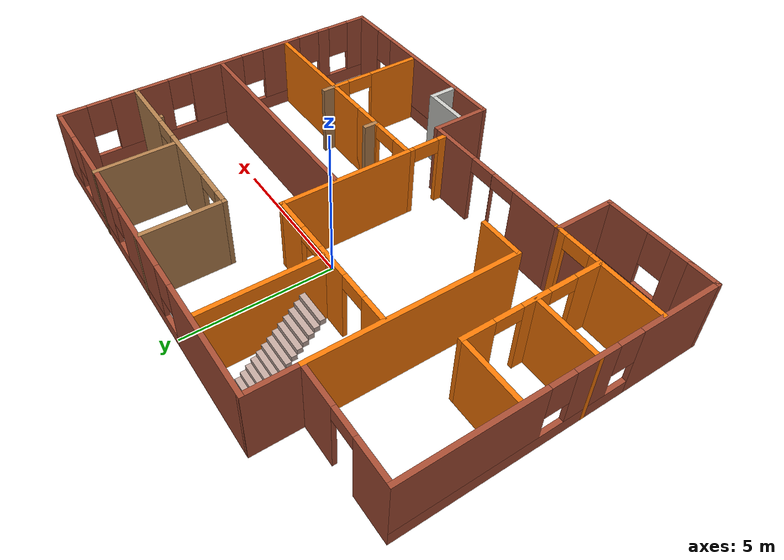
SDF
<?xml version='1.0'?>
<sdf version='1.6'>
  <model name='office'>
    <pose frame=''>0.335982 -0.859919 0 0 -0 0</pose>
    <link name='Stairs_0'>
      <visual name='Stairs_0_Visual_0'>
        <pose frame=''>-3.16704 5.51815 0.083333 0 -0 0</pose>
        <geometry>
          <box>
            <size>1 0.168037 0.166667</size>
          </box>
        </geometry>
        <material>
          <script>
            <uri>file://media/materials/scripts/gazebo.material</uri>
            <name>Gazebo/Grey</name>
          </script>
          <ambient>0.760784 0.662745 0.627451 1</ambient>
        </material>
        <meta>
          <layer>0</layer>
        </meta>
      </visual>
      <collision name='Stairs_0_Collision_0'>
        <geometry>
          <box>
            <size>1 0.168037 0.166667</size>
          </box>
        </geometry>
        <pose frame=''>-3.16704 5.51815 0.083333 0 -0 0</pose>
      </collision>
      <visual name='Stairs_0_Visual_1'>
        <pose frame=''>-3.16704 5.35011 0.25 0 -0 0</pose>
        <geometry>
          <box>
            <size>1 0.168037 0.166667</size>
          </box>
        </geometry>
        <material>
          <script>
            <uri>file://media/materials/scripts/gazebo.material</uri>
            <name>Gazebo/Grey</name>
          </script>
          <ambient>0.760784 0.662745 0.627451 1</ambient>
        </material>
        <meta>
          <layer>0</layer>
        </meta>
      </visual>
      <collision name='Stairs_0_Collision_1'>
        <geometry>
          <box>
            <size>1 0.168037 0.166667</size>
          </box>
        </geometry>
        <pose frame=''>-3.16704 5.35011 0.25 0 -0 0</pose>
      </collision>
      <visual name='Stairs_0_Visual_2'>
        <pose frame=''>-3.16704 5.18207 0.416667 0 -0 0</pose>
        <geometry>
          <box>
            <size>1 0.168037 0.166667</size>
          </box>
        </geometry>
        <material>
          <script>
            <uri>file://media/materials/scripts/gazebo.material</uri>
            <name>Gazebo/Grey</name>
          </script>
          <ambient>0.760784 0.662745 0.627451 1</ambient>
        </material>
        <meta>
          <layer>0</layer>
        </meta>
      </visual>
      <collision name='Stairs_0_Collision_2'>
        <geometry>
          <box>
            <size>1 0.168037 0.166667</size>
          </box>
        </geometry>
        <pose frame=''>-3.16704 5.18207 0.416667 0 -0 0</pose>
      </collision>
      <visual name='Stairs_0_Visual_3'>
        <pose frame=''>-3.16704 5.01404 0.583333 0 -0 0</pose>
        <geometry>
          <box>
            <size>1 0.168037 0.166667</size>
          </box>
        </geometry>
        <material>
          <script>
            <uri>file://media/materials/scripts/gazebo.material</uri>
            <name>Gazebo/Grey</name>
          </script>
          <ambient>0.760784 0.662745 0.627451 1</ambient>
        </material>
        <meta>
          <layer>0</layer>
        </meta>
      </visual>
      <collision name='Stairs_0_Collision_3'>
        <geometry>
          <box>
            <size>1 0.168037 0.166667</size>
          </box>
        </geometry>
        <pose frame=''>-3.16704 5.01404 0.583333 0 -0 0</pose>
      </collision>
      <visual name='Stairs_0_Visual_4'>
        <pose frame=''>-3.16704 4.846 0.75 0 -0 0</pose>
        <geometry>
          <box>
            <size>1 0.168037 0.166667</size>
          </box>
        </geometry>
        <material>
          <script>
            <uri>file://media/materials/scripts/gazebo.material</uri>
            <name>Gazebo/Grey</name>
          </script>
          <ambient>0.760784 0.662745 0.627451 1</ambient>
        </material>
        <meta>
          <layer>0</layer>
        </meta>
      </visual>
      <collision name='Stairs_0_Collision_4'>
        <geometry>
          <box>
            <size>1 0.168037 0.166667</size>
          </box>
        </geometry>
        <pose frame=''>-3.16704 4.846 0.75 0 -0 0</pose>
      </collision>
      <visual name='Stairs_0_Visual_5'>
        <pose frame=''>-3.16704 4.67796 0.916667 0 -0 0</pose>
        <geometry>
          <box>
            <size>1 0.168037 0.166667</size>
          </box>
        </geometry>
        <material>
          <script>
            <uri>file://media/materials/scripts/gazebo.material</uri>
            <name>Gazebo/Grey</name>
          </script>
          <ambient>0.760784 0.662745 0.627451 1</ambient>
        </material>
        <meta>
          <layer>0</layer>
        </meta>
      </visual>
      <collision name='Stairs_0_Collision_5'>
        <geometry>
          <box>
            <size>1 0.168037 0.166667</size>
          </box>
        </geometry>
        <pose frame=''>-3.16704 4.67796 0.916667 0 -0 0</pose>
      </collision>
      <visual name='Stairs_0_Visual_6'>
        <pose frame=''>-3.16704 4.50992 1.08333 0 -0 0</pose>
        <geometry>
          <box>
            <size>1 0.168037 0.166667</size>
          </box>
        </geometry>
        <material>
          <script>
            <uri>file://media/materials/scripts/gazebo.material</uri>
            <name>Gazebo/Grey</name>
          </script>
          <ambient>0.760784 0.662745 0.627451 1</ambient>
        </material>
        <meta>
          <layer>0</layer>
        </meta>
      </visual>
      <collision name='Stairs_0_Collision_6'>
        <geometry>
          <box>
            <size>1 0.168037 0.166667</size>
          </box>
        </geometry>
        <pose frame=''>-3.16704 4.50992 1.08333 0 -0 0</pose>
      </collision>
      <visual name='Stairs_0_Visual_7'>
        <pose frame=''>-3.16704 4.34189 1.25 0 -0 0</pose>
        <geometry>
          <box>
            <size>1 0.168037 0.166667</size>
          </box>
        </geometry>
        <material>
          <script>
            <uri>file://media/materials/scripts/gazebo.material</uri>
            <name>Gazebo/Grey</name>
          </script>
          <ambient>0.760784 0.662745 0.627451 1</ambient>
        </material>
        <meta>
          <layer>0</layer>
        </meta>
      </visual>
      <collision name='Stairs_0_Collision_7'>
        <geometry>
          <box>
            <size>1 0.168037 0.166667</size>
          </box>
        </geometry>
        <pose frame=''>-3.16704 4.34189 1.25 0 -0 0</pose>
      </collision>
      <visual name='Stairs_0_Visual_8'>
        <pose frame=''>-3.16704 4.17385 1.41667 0 -0 0</pose>
        <geometry>
          <box>
            <size>1 0.168037 0.166667</size>
          </box>
        </geometry>
        <material>
          <script>
            <uri>file://media/materials/scripts/gazebo.material</uri>
            <name>Gazebo/Grey</name>
          </script>
          <ambient>0.760784 0.662745 0.627451 1</ambient>
        </material>
        <meta>
          <layer>0</layer>
        </meta>
      </visual>
      <collision name='Stairs_0_Collision_8'>
        <geometry>
          <box>
            <size>1 0.168037 0.166667</size>
          </box>
        </geometry>
        <pose frame=''>-3.16704 4.17385 1.41667 0 -0 0</pose>
      </collision>
      <visual name='Stairs_0_Visual_9'>
        <pose frame=''>-3.16704 4.00581 1.58333 0 -0 0</pose>
        <geometry>
          <box>
            <size>1 0.168037 0.166667</size>
          </box>
        </geometry>
        <material>
          <script>
            <uri>file://media/materials/scripts/gazebo.material</uri>
            <name>Gazebo/Grey</name>
          </script>
          <ambient>0.760784 0.662745 0.627451 1</ambient>
        </material>
        <meta>
          <layer>0</layer>
        </meta>
      </visual>
      <collision name='Stairs_0_Collision_9'>
        <geometry>
          <box>
            <size>1 0.168037 0.166667</size>
          </box>
        </geometry>
        <pose frame=''>-3.16704 4.00581 1.58333 0 -0 0</pose>
      </collision>
      <visual name='Stairs_0_Visual_10'>
        <pose frame=''>-3.16704 3.83778 1.75 0 -0 0</pose>
        <geometry>
          <box>
            <size>1 0.168037 0.166667</size>
          </box>
        </geometry>
        <material>
          <script>
            <uri>file://media/materials/scripts/gazebo.material</uri>
            <name>Gazebo/Grey</name>
          </script>
          <ambient>0.760784 0.662745 0.627451 1</ambient>
        </material>
        <meta>
          <layer>0</layer>
        </meta>
      </visual>
      <collision name='Stairs_0_Collision_10'>
        <geometry>
          <box>
            <size>1 0.168037 0.166667</size>
          </box>
        </geometry>
        <pose frame=''>-3.16704 3.83778 1.75 0 -0 0</pose>
      </collision>
      <visual name='Stairs_0_Visual_11'>
        <pose frame=''>-3.16704 3.66974 1.91667 0 -0 0</pose>
        <geometry>
          <box>
            <size>1 0.168037 0.166667</size>
          </box>
        </geometry>
        <material>
          <script>
            <uri>file://media/materials/scripts/gazebo.material</uri>
            <name>Gazebo/Grey</name>
          </script>
          <ambient>0.760784 0.662745 0.627451 1</ambient>
        </material>
        <meta>
          <layer>0</layer>
        </meta>
      </visual>
      <collision name='Stairs_0_Collision_11'>
        <geometry>
          <box>
            <size>1 0.168037 0.166667</size>
          </box>
        </geometry>
        <pose frame=''>-3.16704 3.66974 1.91667 0 -0 0</pose>
      </collision>
      <visual name='Stairs_0_Visual_12'>
        <pose frame=''>-3.16704 3.5017 2.08333 0 -0 0</pose>
        <geometry>
          <box>
            <size>1 0.168037 0.166667</size>
          </box>
        </geometry>
        <material>
          <script>
            <uri>file://media/materials/scripts/gazebo.material</uri>
            <name>Gazebo/Grey</name>
          </script>
          <ambient>0.760784 0.662745 0.627451 1</ambient>
        </material>
        <meta>
          <layer>0</layer>
        </meta>
      </visual>
      <collision name='Stairs_0_Collision_12'>
        <geometry>
          <box>
            <size>1 0.168037 0.166667</size>
          </box>
        </geometry>
        <pose frame=''>-3.16704 3.5017 2.08333 0 -0 0</pose>
      </collision>
      <visual name='Stairs_0_Visual_13'>
        <pose frame=''>-3.16704 3.33366 2.25 0 -0 0</pose>
        <geometry>
          <box>
            <size>1 0.168037 0.166667</size>
          </box>
        </geometry>
        <material>
          <script>
            <uri>file://media/materials/scripts/gazebo.material</uri>
            <name>Gazebo/Grey</name>
          </script>
          <ambient>0.760784 0.662745 0.627451 1</ambient>
        </material>
        <meta>
          <layer>0</layer>
        </meta>
      </visual>
      <collision name='Stairs_0_Collision_13'>
        <geometry>
          <box>
            <size>1 0.168037 0.166667</size>
          </box>
        </geometry>
        <pose frame=''>-3.16704 3.33366 2.25 0 -0 0</pose>
      </collision>
      <visual name='Stairs_0_Visual_14'>
        <pose frame=''>-3.16704 3.16563 2.41667 0 -0 0</pose>
        <geometry>
          <box>
            <size>1 0.168037 0.166667</size>
          </box>
        </geometry>
        <material>
          <script>
            <uri>file://media/materials/scripts/gazebo.material</uri>
            <name>Gazebo/Grey</name>
          </script>
          <ambient>0.760784 0.662745 0.627451 1</ambient>
        </material>
        <meta>
          <layer>0</layer>
        </meta>
      </visual>
      <collision name='Stairs_0_Collision_14'>
        <geometry>
          <box>
            <size>1 0.168037 0.166667</size>
          </box>
        </geometry>
        <pose frame=''>-3.16704 3.16563 2.41667 0 -0 0</pose>
      </collision>
    </link>
    <link name='Wall_10'>
      <collision name='Wall_10_Collision'>
        <geometry>
          <box>
            <size>1 0.15 2.5</size>
          </box>
        </geometry>
        <pose frame=''>0 0 1.25 0 -0 0</pose>
      </collision>
      <visual name='Wall_10_Visual'>
        <pose frame=''>0 0 1.25 0 -0 0</pose>
        <geometry>
          <box>
            <size>1 0.15 2.5</size>
          </box>
        </geometry>
        <material>
          <script>
            <uri>file://media/materials/scripts/gazebo.material</uri>
            <name>Gazebo/Bricks</name>
          </script>
          <ambient>1 1 1 1</ambient>
        </material>
        <meta>
          <layer>0</layer>
        </meta>
      </visual>
      <pose frame=''>-7.67457 -5.85749 0 0 -0 3.14159</pose>
    </link>
    <link name='Wall_11'>
      <pose frame=''>-8.09957 -0.807493 0 0 -0 1.5708</pose>
      <visual name='Wall_11_Visual_0'>
        <pose frame=''>-3.7208 0 1.25 0 -0 0</pose>
        <geometry>
          <box>
            <size>2.8084 0.15 2.5</size>
          </box>
        </geometry>
        <material>
          <script>
            <uri>file://media/materials/scripts/gazebo.material</uri>
            <name>Gazebo/Bricks</name>
          </script>
          <ambient>1 1 1 1</ambient>
        </material>
        <meta>
          <layer>0</layer>
        </meta>
      </visual>
      <collision name='Wall_11_Collision_0'>
        <geometry>
          <box>
            <size>2.8084 0.15 2.5</size>
          </box>
        </geometry>
        <pose frame=''>-3.7208 0 1.25 0 -0 0</pose>
      </collision>
      <visual name='Wall_11_Visual_1'>
        <pose frame=''>1.4042 0 0.25 0 -0 0</pose>
        <geometry>
          <box>
            <size>7.4416 0.15 0.5</size>
          </box>
        </geometry>
        <material>
          <script>
            <uri>file://media/materials/scripts/gazebo.material</uri>
            <name>Gazebo/Bricks</name>
          </script>
          <ambient>1 1 1 1</ambient>
        </material>
        <meta>
          <layer>0</layer>
        </meta>
      </visual>
      <collision name='Wall_11_Collision_1'>
        <geometry>
          <box>
            <size>7.4416 0.15 0.5</size>
          </box>
        </geometry>
        <pose frame=''>1.4042 0 0.25 0 -0 0</pose>
      </collision>
      <visual name='Wall_11_Visual_2'>
        <pose frame=''>-0.81473 0 1.5 0 -0 0</pose>
        <geometry>
          <box>
            <size>1.40375 0.15 2</size>
          </box>
        </geometry>
        <material>
          <script>
            <uri>file://media/materials/scripts/gazebo.material</uri>
            <name>Gazebo/Bricks</name>
          </script>
          <ambient>1 1 1 1</ambient>
        </material>
        <meta>
          <layer>0</layer>
        </meta>
      </visual>
      <collision name='Wall_11_Collision_2'>
        <geometry>
          <box>
            <size>1.40375 0.15 2</size>
          </box>
        </geometry>
        <pose frame=''>-0.81473 0 1.5 0 -0 0</pose>
      </collision>
      <visual name='Wall_11_Visual_3'>
        <pose frame=''>2.90607 0 1.5 0 -0 0</pose>
        <geometry>
          <box>
            <size>4.43786 0.15 2</size>
          </box>
        </geometry>
        <material>
          <script>
            <uri>file://media/materials/scripts/gazebo.material</uri>
            <name>Gazebo/Bricks</name>
          </script>
          <ambient>1 1 1 1</ambient>
        </material>
        <meta>
          <layer>0</layer>
        </meta>
      </visual>
      <collision name='Wall_11_Collision_3'>
        <geometry>
          <box>
            <size>4.43786 0.15 2</size>
          </box>
        </geometry>
        <pose frame=''>2.90607 0 1.5 0 -0 0</pose>
      </collision>
      <visual name='Wall_11_Visual_4'>
        <pose frame=''>-1.9166 0 1.9 0 -0 0</pose>
        <geometry>
          <box>
            <size>0.8 0.15 1.2</size>
          </box>
        </geometry>
        <material>
          <script>
            <uri>file://media/materials/scripts/gazebo.material</uri>
            <name>Gazebo/Bricks</name>
          </script>
          <ambient>1 1 1 1</ambient>
        </material>
        <meta>
          <layer>0</layer>
        </meta>
      </visual>
      <collision name='Wall_11_Collision_4'>
        <geometry>
          <box>
            <size>0.8 0.15 1.2</size>
          </box>
        </geometry>
        <pose frame=''>-1.9166 0 1.9 0 -0 0</pose>
      </collision>
      <visual name='Wall_11_Visual_5'>
        <pose frame=''>0.287144 0 1.9 0 -0 0</pose>
        <geometry>
          <box>
            <size>0.8 0.15 1.2</size>
          </box>
        </geometry>
        <material>
          <script>
            <uri>file://media/materials/scripts/gazebo.material</uri>
            <name>Gazebo/Bricks</name>
          </script>
          <ambient>1 1 1 1</ambient>
        </material>
        <meta>
          <layer>0</layer>
        </meta>
      </visual>
      <collision name='Wall_11_Collision_5'>
        <geometry>
          <box>
            <size>0.8 0.15 1.2</size>
          </box>
        </geometry>
        <pose frame=''>0.287144 0 1.9 0 -0 0</pose>
      </collision>
    </link>
    <link name='Wall_12'>
      <pose frame=''>-6.29957 4.24251 0 0 -0 0</pose>
      <visual name='Wall_12_Visual_0'>
        <pose frame=''>-1.17034 0 1.25 0 -0 0</pose>
        <geometry>
          <box>
            <size>1.40932 0.15 2.5</size>
          </box>
        </geometry>
        <material>
          <script>
            <uri>file://media/materials/scripts/gazebo.material</uri>
            <name>Gazebo/Bricks</name>
          </script>
          <ambient>1 1 1 1</ambient>
        </material>
        <meta>
          <layer>0</layer>
        </meta>
      </visual>
      <collision name='Wall_12_Collision_0'>
        <geometry>
          <box>
            <size>1.40932 0.15 2.5</size>
          </box>
        </geometry>
        <pose frame=''>-1.17034 0 1.25 0 -0 0</pose>
      </collision>
      <visual name='Wall_12_Visual_1'>
        <pose frame=''>1.15466 0 1.25 0 -0 0</pose>
        <geometry>
          <box>
            <size>1.44068 0.15 2.5</size>
          </box>
        </geometry>
        <material>
          <script>
            <uri>file://media/materials/scripts/gazebo.material</uri>
            <name>Gazebo/Bricks</name>
          </script>
          <ambient>1 1 1 1</ambient>
        </material>
        <meta>
          <layer>0</layer>
        </meta>
      </visual>
      <collision name='Wall_12_Collision_1'>
        <geometry>
          <box>
            <size>1.44068 0.15 2.5</size>
          </box>
        </geometry>
        <pose frame=''>1.15466 0 1.25 0 -0 0</pose>
      </collision>
      <visual name='Wall_12_Visual_2'>
        <pose frame=''>-0.015683 0 2.25 0 -0 0</pose>
        <geometry>
          <box>
            <size>0.9 0.15 0.5</size>
          </box>
        </geometry>
        <material>
          <script>
            <uri>file://media/materials/scripts/gazebo.material</uri>
            <name>Gazebo/Bricks</name>
          </script>
          <ambient>1 1 1 1</ambient>
        </material>
        <meta>
          <layer>0</layer>
        </meta>
      </visual>
      <collision name='Wall_12_Collision_2'>
        <geometry>
          <box>
            <size>0.9 0.15 0.5</size>
          </box>
        </geometry>
        <pose frame=''>-0.015683 0 2.25 0 -0 0</pose>
      </collision>
    </link>
    <link name='Wall_13'>
      <collision name='Wall_13_Collision'>
        <geometry>
          <box>
            <size>1.75 0.15 2.5</size>
          </box>
        </geometry>
        <pose frame=''>0 0 1.25 0 -0 0</pose>
      </collision>
      <visual name='Wall_13_Visual'>
        <pose frame=''>0 0 1.25 0 -0 0</pose>
        <geometry>
          <box>
            <size>1.75 0.15 2.5</size>
          </box>
        </geometry>
        <material>
          <script>
            <uri>file://media/materials/scripts/gazebo.material</uri>
            <name>Gazebo/Bricks</name>
          </script>
          <ambient>1 1 1 1</ambient>
        </material>
        <meta>
          <layer>0</layer>
        </meta>
      </visual>
      <pose frame=''>-4.49957 5.04251 0 0 -0 1.5708</pose>
    </link>
    <link name='Wall_14'>
      <pose frame=''>1.80043 5.84251 0 0 -0 0</pose>
      <visual name='Wall_14_Visual_0'>
        <pose frame=''>-4.36709 0 1.25 0 -0 0</pose>
        <geometry>
          <box>
            <size>4.01582 0.15 2.5</size>
          </box>
        </geometry>
        <material>
          <script>
            <uri>file://media/materials/scripts/gazebo.material</uri>
            <name>Gazebo/Bricks</name>
          </script>
          <ambient>1 1 1 1</ambient>
        </material>
        <meta>
          <layer>0</layer>
        </meta>
      </visual>
      <collision name='Wall_14_Collision_0'>
        <geometry>
          <box>
            <size>4.01582 0.15 2.5</size>
          </box>
        </geometry>
        <pose frame=''>-4.36709 0 1.25 0 -0 0</pose>
      </collision>
      <visual name='Wall_14_Visual_1'>
        <pose frame=''>2.00791 0 0.25 0 -0 0</pose>
        <geometry>
          <box>
            <size>8.73418 0.15 0.5</size>
          </box>
        </geometry>
        <material>
          <script>
            <uri>file://media/materials/scripts/gazebo.material</uri>
            <name>Gazebo/Bricks</name>
          </script>
          <ambient>1 1 1 1</ambient>
        </material>
        <meta>
          <layer>0</layer>
        </meta>
      </visual>
      <collision name='Wall_14_Collision_1'>
        <geometry>
          <box>
            <size>8.73418 0.15 0.5</size>
          </box>
        </geometry>
        <pose frame=''>2.00791 0 0.25 0 -0 0</pose>
      </collision>
      <visual name='Wall_14_Visual_2'>
        <pose frame=''>-0.245155 0 1.5 0 -0 0</pose>
        <geometry>
          <box>
            <size>2.62805 0.15 2</size>
          </box>
        </geometry>
        <material>
          <script>
            <uri>file://media/materials/scripts/gazebo.material</uri>
            <name>Gazebo/Bricks</name>
          </script>
          <ambient>1 1 1 1</ambient>
        </material>
        <meta>
          <layer>0</layer>
        </meta>
      </visual>
      <collision name='Wall_14_Collision_2'>
        <geometry>
          <box>
            <size>2.62805 0.15 2</size>
          </box>
        </geometry>
        <pose frame=''>-0.245155 0 1.5 0 -0 0</pose>
      </collision>
      <visual name='Wall_14_Visual_3'>
        <pose frame=''>3.008 0 1.5 0 -0 0</pose>
        <geometry>
          <box>
            <size>2.27825 0.15 2</size>
          </box>
        </geometry>
        <material>
          <script>
            <uri>file://media/materials/scripts/gazebo.material</uri>
            <name>Gazebo/Bricks</name>
          </script>
          <ambient>1 1 1 1</ambient>
        </material>
        <meta>
          <layer>0</layer>
        </meta>
      </visual>
      <collision name='Wall_14_Collision_3'>
        <geometry>
          <box>
            <size>2.27825 0.15 2</size>
          </box>
        </geometry>
        <pose frame=''>3.008 0 1.5 0 -0 0</pose>
      </collision>
      <visual name='Wall_14_Visual_4'>
        <pose frame=''>5.66106 0 1.5 0 -0 0</pose>
        <geometry>
          <box>
            <size>1.42788 0.15 2</size>
          </box>
        </geometry>
        <material>
          <script>
            <uri>file://media/materials/scripts/gazebo.material</uri>
            <name>Gazebo/Bricks</name>
          </script>
          <ambient>1 1 1 1</ambient>
        </material>
        <meta>
          <layer>0</layer>
        </meta>
      </visual>
      <collision name='Wall_14_Collision_4'>
        <geometry>
          <box>
            <size>1.42788 0.15 2</size>
          </box>
        </geometry>
        <pose frame=''>5.66106 0 1.5 0 -0 0</pose>
      </collision>
      <visual name='Wall_14_Visual_5'>
        <pose frame=''>-1.95918 0 1.9 0 -0 0</pose>
        <geometry>
          <box>
            <size>0.8 0.15 1.2</size>
          </box>
        </geometry>
        <material>
          <script>
            <uri>file://media/materials/scripts/gazebo.material</uri>
            <name>Gazebo/Bricks</name>
          </script>
          <ambient>1 1 1 1</ambient>
        </material>
        <meta>
          <layer>0</layer>
        </meta>
      </visual>
      <collision name='Wall_14_Collision_5'>
        <geometry>
          <box>
            <size>0.8 0.15 1.2</size>
          </box>
        </geometry>
        <pose frame=''>-1.95918 0 1.9 0 -0 0</pose>
      </collision>
      <visual name='Wall_14_Visual_6'>
        <pose frame=''>1.46887 0 1.9 0 -0 0</pose>
        <geometry>
          <box>
            <size>0.8 0.15 1.2</size>
          </box>
        </geometry>
        <material>
          <script>
            <uri>file://media/materials/scripts/gazebo.material</uri>
            <name>Gazebo/Bricks</name>
          </script>
          <ambient>1 1 1 1</ambient>
        </material>
        <meta>
          <layer>0</layer>
        </meta>
      </visual>
      <collision name='Wall_14_Collision_6'>
        <geometry>
          <box>
            <size>0.8 0.15 1.2</size>
          </box>
        </geometry>
        <pose frame=''>1.46887 0 1.9 0 -0 0</pose>
      </collision>
      <visual name='Wall_14_Visual_7'>
        <pose frame=''>4.54712 0 1.9 0 -0 0</pose>
        <geometry>
          <box>
            <size>0.8 0.15 1.2</size>
          </box>
        </geometry>
        <material>
          <script>
            <uri>file://media/materials/scripts/gazebo.material</uri>
            <name>Gazebo/Bricks</name>
          </script>
          <ambient>1 1 1 1</ambient>
        </material>
        <meta>
          <layer>0</layer>
        </meta>
      </visual>
      <collision name='Wall_14_Collision_7'>
        <geometry>
          <box>
            <size>0.8 0.15 1.2</size>
          </box>
        </geometry>
        <pose frame=''>4.54712 0 1.9 0 -0 0</pose>
      </collision>
    </link>
    <link name='Wall_15'>
      <pose frame=''>8.10043 0.042507 0 0 0 -1.5708</pose>
      <visual name='Wall_15_Visual_0'>
        <pose frame=''>-5.39213 0 1.25 0 -0 0</pose>
        <geometry>
          <box>
            <size>0.965738 0.15 2.5</size>
          </box>
        </geometry>
        <material>
          <script>
            <uri>file://media/materials/scripts/gazebo.material</uri>
            <name>Gazebo/Bricks</name>
          </script>
          <ambient>1 1 1 1</ambient>
        </material>
        <meta>
          <layer>0</layer>
        </meta>
      </visual>
      <collision name='Wall_15_Collision_0'>
        <geometry>
          <box>
            <size>0.965738 0.15 2.5</size>
          </box>
        </geometry>
        <pose frame=''>-5.39213 0 1.25 0 -0 0</pose>
      </collision>
      <visual name='Wall_15_Visual_1'>
        <pose frame=''>0.482869 0 0.25 0 -0 0</pose>
        <geometry>
          <box>
            <size>10.7843 0.15 0.5</size>
          </box>
        </geometry>
        <material>
          <script>
            <uri>file://media/materials/scripts/gazebo.material</uri>
            <name>Gazebo/Bricks</name>
          </script>
          <ambient>1 1 1 1</ambient>
        </material>
        <meta>
          <layer>0</layer>
        </meta>
      </visual>
      <collision name='Wall_15_Collision_1'>
        <geometry>
          <box>
            <size>10.7843 0.15 0.5</size>
          </box>
        </geometry>
        <pose frame=''>0.482869 0 0.25 0 -0 0</pose>
      </collision>
      <visual name='Wall_15_Visual_2'>
        <pose frame=''>-3.09257 0 1.5 0 -0 0</pose>
        <geometry>
          <box>
            <size>2.03339 0.15 2</size>
          </box>
        </geometry>
        <material>
          <script>
            <uri>file://media/materials/scripts/gazebo.material</uri>
            <name>Gazebo/Bricks</name>
          </script>
          <ambient>1 1 1 1</ambient>
        </material>
        <meta>
          <layer>0</layer>
        </meta>
      </visual>
      <collision name='Wall_15_Collision_2'>
        <geometry>
          <box>
            <size>2.03339 0.15 2</size>
          </box>
        </geometry>
        <pose frame=''>-3.09257 0 1.5 0 -0 0</pose>
      </collision>
      <visual name='Wall_15_Visual_3'>
        <pose frame=''>-0.276667 0 1.5 0 -0 0</pose>
        <geometry>
          <box>
            <size>1.99841 0.15 2</size>
          </box>
        </geometry>
        <material>
          <script>
            <uri>file://media/materials/scripts/gazebo.material</uri>
            <name>Gazebo/Bricks</name>
          </script>
          <ambient>1 1 1 1</ambient>
        </material>
        <meta>
          <layer>0</layer>
        </meta>
      </visual>
      <collision name='Wall_15_Collision_3'>
        <geometry>
          <box>
            <size>1.99841 0.15 2</size>
          </box>
        </geometry>
        <pose frame=''>-0.276667 0 1.5 0 -0 0</pose>
      </collision>
      <visual name='Wall_15_Visual_4'>
        <pose frame=''>2.27688 0 1.5 0 -0 0</pose>
        <geometry>
          <box>
            <size>1.50869 0.15 2</size>
          </box>
        </geometry>
        <material>
          <script>
            <uri>file://media/materials/scripts/gazebo.material</uri>
            <name>Gazebo/Bricks</name>
          </script>
          <ambient>1 1 1 1</ambient>
        </material>
        <meta>
          <layer>0</layer>
        </meta>
      </visual>
      <collision name='Wall_15_Collision_4'>
        <geometry>
          <box>
            <size>1.50869 0.15 2</size>
          </box>
        </geometry>
        <pose frame=''>2.27688 0 1.5 0 -0 0</pose>
      </collision>
      <visual name='Wall_15_Visual_5'>
        <pose frame=''>4.06087 0 1.5 0 -0 0</pose>
        <geometry>
          <box>
            <size>0.459284 0.15 2</size>
          </box>
        </geometry>
        <material>
          <script>
            <uri>file://media/materials/scripts/gazebo.material</uri>
            <name>Gazebo/Bricks</name>
          </script>
          <ambient>1 1 1 1</ambient>
        </material>
        <meta>
          <layer>0</layer>
        </meta>
      </visual>
      <collision name='Wall_15_Collision_5'>
        <geometry>
          <box>
            <size>0.459284 0.15 2</size>
          </box>
        </geometry>
        <pose frame=''>4.06087 0 1.5 0 -0 0</pose>
      </collision>
      <visual name='Wall_15_Visual_6'>
        <pose frame=''>5.48276 0 1.5 0 -0 0</pose>
        <geometry>
          <box>
            <size>0.784489 0.15 2</size>
          </box>
        </geometry>
        <material>
          <script>
            <uri>file://media/materials/scripts/gazebo.material</uri>
            <name>Gazebo/Bricks</name>
          </script>
          <ambient>1 1 1 1</ambient>
        </material>
        <meta>
          <layer>0</layer>
        </meta>
      </visual>
      <collision name='Wall_15_Collision_6'>
        <geometry>
          <box>
            <size>0.784489 0.15 2</size>
          </box>
        </geometry>
        <pose frame=''>5.48276 0 1.5 0 -0 0</pose>
      </collision>
      <visual name='Wall_15_Visual_7'>
        <pose frame=''>-4.50926 0 1.9 0 -0 0</pose>
        <geometry>
          <box>
            <size>0.8 0.15 1.2</size>
          </box>
        </geometry>
        <material>
          <script>
            <uri>file://media/materials/scripts/gazebo.material</uri>
            <name>Gazebo/Bricks</name>
          </script>
          <ambient>1 1 1 1</ambient>
        </material>
        <meta>
          <layer>0</layer>
        </meta>
      </visual>
      <collision name='Wall_15_Collision_7'>
        <geometry>
          <box>
            <size>0.8 0.15 1.2</size>
          </box>
        </geometry>
        <pose frame=''>-4.50926 0 1.9 0 -0 0</pose>
      </collision>
      <visual name='Wall_15_Visual_8'>
        <pose frame=''>-1.67587 0 1.9 0 -0 0</pose>
        <geometry>
          <box>
            <size>0.8 0.15 1.2</size>
          </box>
        </geometry>
        <material>
          <script>
            <uri>file://media/materials/scripts/gazebo.material</uri>
            <name>Gazebo/Bricks</name>
          </script>
          <ambient>1 1 1 1</ambient>
        </material>
        <meta>
          <layer>0</layer>
        </meta>
      </visual>
      <collision name='Wall_15_Collision_8'>
        <geometry>
          <box>
            <size>0.8 0.15 1.2</size>
          </box>
        </geometry>
        <pose frame=''>-1.67587 0 1.9 0 -0 0</pose>
      </collision>
      <visual name='Wall_15_Visual_9'>
        <pose frame=''>1.12254 0 1.9 0 -0 0</pose>
        <geometry>
          <box>
            <size>0.8 0.15 1.2</size>
          </box>
        </geometry>
        <material>
          <script>
            <uri>file://media/materials/scripts/gazebo.material</uri>
            <name>Gazebo/Bricks</name>
          </script>
          <ambient>1 1 1 1</ambient>
        </material>
        <meta>
          <layer>0</layer>
        </meta>
      </visual>
      <collision name='Wall_15_Collision_9'>
        <geometry>
          <box>
            <size>0.8 0.15 1.2</size>
          </box>
        </geometry>
        <pose frame=''>1.12254 0 1.9 0 -0 0</pose>
      </collision>
      <visual name='Wall_15_Visual_10'>
        <pose frame=''>3.43123 0 1.9 0 -0 0</pose>
        <geometry>
          <box>
            <size>0.8 0.15 1.2</size>
          </box>
        </geometry>
        <material>
          <script>
            <uri>file://media/materials/scripts/gazebo.material</uri>
            <name>Gazebo/Bricks</name>
          </script>
          <ambient>1 1 1 1</ambient>
        </material>
        <meta>
          <layer>0</layer>
        </meta>
      </visual>
      <collision name='Wall_15_Collision_10'>
        <geometry>
          <box>
            <size>0.8 0.15 1.2</size>
          </box>
        </geometry>
        <pose frame=''>3.43123 0 1.9 0 -0 0</pose>
      </collision>
      <visual name='Wall_15_Visual_11'>
        <pose frame=''>4.69051 0 1.9 0 -0 0</pose>
        <geometry>
          <box>
            <size>0.8 0.15 1.2</size>
          </box>
        </geometry>
        <material>
          <script>
            <uri>file://media/materials/scripts/gazebo.material</uri>
            <name>Gazebo/Bricks</name>
          </script>
          <ambient>1 1 1 1</ambient>
        </material>
        <meta>
          <layer>0</layer>
        </meta>
      </visual>
      <collision name='Wall_15_Collision_11'>
        <geometry>
          <box>
            <size>0.8 0.15 1.2</size>
          </box>
        </geometry>
        <pose frame=''>4.69051 0 1.9 0 -0 0</pose>
      </collision>
    </link>
    <link name='Wall_21'>
      <pose frame=''>4.55043 -5.75749 0 0 -0 3.14159</pose>
      <visual name='Wall_21_Visual_0'>
        <pose frame=''>-2.99851 0 1.25 0 -0 0</pose>
        <geometry>
          <box>
            <size>1.25298 0.15 2.5</size>
          </box>
        </geometry>
        <material>
          <script>
            <uri>file://media/materials/scripts/gazebo.material</uri>
            <name>Gazebo/Bricks</name>
          </script>
          <ambient>1 1 1 1</ambient>
        </material>
        <meta>
          <layer>0</layer>
        </meta>
      </visual>
      <collision name='Wall_21_Collision_0'>
        <geometry>
          <box>
            <size>1.25298 0.15 2.5</size>
          </box>
        </geometry>
        <pose frame=''>-2.99851 0 1.25 0 -0 0</pose>
      </collision>
      <visual name='Wall_21_Visual_1'>
        <pose frame=''>0.626488 0 0.25 0 -0 0</pose>
        <geometry>
          <box>
            <size>5.99702 0.15 0.5</size>
          </box>
        </geometry>
        <material>
          <script>
            <uri>file://media/materials/scripts/gazebo.material</uri>
            <name>Gazebo/Bricks</name>
          </script>
          <ambient>1 1 1 1</ambient>
        </material>
        <meta>
          <layer>0</layer>
        </meta>
      </visual>
      <collision name='Wall_21_Collision_1'>
        <geometry>
          <box>
            <size>5.99702 0.15 0.5</size>
          </box>
        </geometry>
        <pose frame=''>0.626488 0 0.25 0 -0 0</pose>
      </collision>
      <visual name='Wall_21_Visual_2'>
        <pose frame=''>1.02649 0 1.5 0 -0 0</pose>
        <geometry>
          <box>
            <size>5.19702 0.15 2</size>
          </box>
        </geometry>
        <material>
          <script>
            <uri>file://media/materials/scripts/gazebo.material</uri>
            <name>Gazebo/Bricks</name>
          </script>
          <ambient>1 1 1 1</ambient>
        </material>
        <meta>
          <layer>0</layer>
        </meta>
      </visual>
      <collision name='Wall_21_Collision_2'>
        <geometry>
          <box>
            <size>5.19702 0.15 2</size>
          </box>
        </geometry>
        <pose frame=''>1.02649 0 1.5 0 -0 0</pose>
      </collision>
      <visual name='Wall_21_Visual_3'>
        <pose frame=''>-1.97202 0 1.9 0 -0 0</pose>
        <geometry>
          <box>
            <size>0.8 0.15 1.2</size>
          </box>
        </geometry>
        <material>
          <script>
            <uri>file://media/materials/scripts/gazebo.material</uri>
            <name>Gazebo/Bricks</name>
          </script>
          <ambient>1 1 1 1</ambient>
        </material>
        <meta>
          <layer>0</layer>
        </meta>
      </visual>
      <collision name='Wall_21_Collision_3'>
        <geometry>
          <box>
            <size>0.8 0.15 1.2</size>
          </box>
        </geometry>
        <pose frame=''>-1.97202 0 1.9 0 -0 0</pose>
      </collision>
    </link>
    <link name='Wall_22'>
      <collision name='Wall_22_Collision'>
        <geometry>
          <box>
            <size>2 0.15 2.5</size>
          </box>
        </geometry>
        <pose frame=''>0 0 1.25 0 -0 0</pose>
      </collision>
      <visual name='Wall_22_Visual'>
        <pose frame=''>0 0 1.25 0 -0 0</pose>
        <geometry>
          <box>
            <size>2 0.15 2.5</size>
          </box>
        </geometry>
        <material>
          <script>
            <uri>file://media/materials/scripts/gazebo.material</uri>
            <name>Gazebo/Bricks</name>
          </script>
          <ambient>1 1 1 1</ambient>
        </material>
        <meta>
          <layer>0</layer>
        </meta>
      </visual>
      <pose frame=''>1.00043 -4.83249 0 0 -0 1.5708</pose>
    </link>
    <link name='Wall_23'>
      <pose frame=''>-1.67457 -3.90749 0 0 -0 3.14159</pose>
      <visual name='Wall_23_Visual_0'>
        <pose frame=''>-1.81572 0 1.25 0 -0 0</pose>
        <geometry>
          <box>
            <size>1.86857 0.15 2.5</size>
          </box>
        </geometry>
        <material>
          <script>
            <uri>file://media/materials/scripts/gazebo.material</uri>
            <name>Gazebo/Bricks</name>
          </script>
          <ambient>1 1 1 1</ambient>
        </material>
        <meta>
          <layer>0</layer>
        </meta>
      </visual>
      <collision name='Wall_23_Collision_0'>
        <geometry>
          <box>
            <size>1.86857 0.15 2.5</size>
          </box>
        </geometry>
        <pose frame=''>-1.81572 0 1.25 0 -0 0</pose>
      </collision>
      <visual name='Wall_23_Visual_1'>
        <pose frame=''>0.023306 0 1.25 0 -0 0</pose>
        <geometry>
          <box>
            <size>0.009483 0.15 2.5</size>
          </box>
        </geometry>
        <material>
          <script>
            <uri>file://media/materials/scripts/gazebo.material</uri>
            <name>Gazebo/Bricks</name>
          </script>
          <ambient>1 1 1 1</ambient>
        </material>
        <meta>
          <layer>0</layer>
        </meta>
      </visual>
      <collision name='Wall_23_Collision_1'>
        <geometry>
          <box>
            <size>0.009483 0.15 2.5</size>
          </box>
        </geometry>
        <pose frame=''>0.023306 0 1.25 0 -0 0</pose>
      </collision>
      <visual name='Wall_23_Visual_2'>
        <pose frame=''>1.83902 0 1.25 0 -0 0</pose>
        <geometry>
          <box>
            <size>1.82195 0.15 2.5</size>
          </box>
        </geometry>
        <material>
          <script>
            <uri>file://media/materials/scripts/gazebo.material</uri>
            <name>Gazebo/Bricks</name>
          </script>
          <ambient>1 1 1 1</ambient>
        </material>
        <meta>
          <layer>0</layer>
        </meta>
      </visual>
      <collision name='Wall_23_Collision_2'>
        <geometry>
          <box>
            <size>1.82195 0.15 2.5</size>
          </box>
        </geometry>
        <pose frame=''>1.83902 0 1.25 0 -0 0</pose>
      </collision>
      <visual name='Wall_23_Visual_3'>
        <pose frame=''>-0.431435 0 2.25 0 -0 0</pose>
        <geometry>
          <box>
            <size>0.9 0.15 0.5</size>
          </box>
        </geometry>
        <material>
          <script>
            <uri>file://media/materials/scripts/gazebo.material</uri>
            <name>Gazebo/Bricks</name>
          </script>
          <ambient>1 1 1 1</ambient>
        </material>
        <meta>
          <layer>0</layer>
        </meta>
      </visual>
      <collision name='Wall_23_Collision_3'>
        <geometry>
          <box>
            <size>0.9 0.15 0.5</size>
          </box>
        </geometry>
        <pose frame=''>-0.431435 0 2.25 0 -0 0</pose>
      </collision>
      <visual name='Wall_23_Visual_4'>
        <pose frame=''>0.478048 0 2.25 0 -0 0</pose>
        <geometry>
          <box>
            <size>0.9 0.15 0.5</size>
          </box>
        </geometry>
        <material>
          <script>
            <uri>file://media/materials/scripts/gazebo.material</uri>
            <name>Gazebo/Bricks</name>
          </script>
          <ambient>1 1 1 1</ambient>
        </material>
        <meta>
          <layer>0</layer>
        </meta>
      </visual>
      <collision name='Wall_23_Collision_4'>
        <geometry>
          <box>
            <size>0.9 0.15 0.5</size>
          </box>
        </geometry>
        <pose frame=''>0.478048 0 2.25 0 -0 0</pose>
      </collision>
    </link>
    <link name='Wall_25'>
      <pose frame=''>-5.14957 -3.90749 0 0 -0 3.14159</pose>
      <visual name='Wall_25_Visual_0'>
        <pose frame=''>-0.656831 0 1.25 0 -0 0</pose>
        <geometry>
          <box>
            <size>0.436339 0.15 2.5</size>
          </box>
        </geometry>
        <material>
          <script>
            <uri>file://media/materials/scripts/gazebo.material</uri>
            <name>Gazebo/Grey</name>
          </script>
          <ambient>0.996078 0.47451 0.0196078 1</ambient>
        </material>
        <meta>
          <layer>0</layer>
        </meta>
      </visual>
      <collision name='Wall_25_Collision_0'>
        <geometry>
          <box>
            <size>0.436339 0.15 2.5</size>
          </box>
        </geometry>
        <pose frame=''>-0.656831 0 1.25 0 -0 0</pose>
      </collision>
      <visual name='Wall_25_Visual_1'>
        <pose frame=''>0.668169 0 1.25 0 -0 0</pose>
        <geometry>
          <box>
            <size>0.413661 0.15 2.5</size>
          </box>
        </geometry>
        <material>
          <script>
            <uri>file://media/materials/scripts/gazebo.material</uri>
            <name>Gazebo/Grey</name>
          </script>
          <ambient>0.996078 0.47451 0.0196078 1</ambient>
        </material>
        <meta>
          <layer>0</layer>
        </meta>
      </visual>
      <collision name='Wall_25_Collision_1'>
        <geometry>
          <box>
            <size>0.413661 0.15 2.5</size>
          </box>
        </geometry>
        <pose frame=''>0.668169 0 1.25 0 -0 0</pose>
      </collision>
      <visual name='Wall_25_Visual_2'>
        <pose frame=''>0.011339 0 2.25 0 -0 0</pose>
        <geometry>
          <box>
            <size>0.9 0.15 0.5</size>
          </box>
        </geometry>
        <material>
          <script>
            <uri>file://media/materials/scripts/gazebo.material</uri>
            <name>Gazebo/Grey</name>
          </script>
          <ambient>0.996078 0.47451 0.0196078 1</ambient>
        </material>
        <meta>
          <layer>0</layer>
        </meta>
      </visual>
      <collision name='Wall_25_Collision_2'>
        <geometry>
          <box>
            <size>0.9 0.15 0.5</size>
          </box>
        </geometry>
        <pose frame=''>0.011339 0 2.25 0 -0 0</pose>
      </collision>
    </link>
    <link name='Wall_26'>
      <pose frame=''>-5.94957 -1.60749 0 0 -0 1.5708</pose>
      <visual name='Wall_26_Visual_0'>
        <pose frame=''>-1.90084 0 1.25 0 -0 0</pose>
        <geometry>
          <box>
            <size>0.948317 0.15 2.5</size>
          </box>
        </geometry>
        <material>
          <script>
            <uri>file://media/materials/scripts/gazebo.material</uri>
            <name>Gazebo/Grey</name>
          </script>
          <ambient>0.996078 0.47451 0.0196078 1</ambient>
        </material>
        <meta>
          <layer>0</layer>
        </meta>
      </visual>
      <collision name='Wall_26_Collision_0'>
        <geometry>
          <box>
            <size>0.948317 0.15 2.5</size>
          </box>
        </geometry>
        <pose frame=''>-1.90084 0 1.25 0 -0 0</pose>
      </collision>
      <visual name='Wall_26_Visual_1'>
        <pose frame=''>-0.0672 0 1.25 0 -0 0</pose>
        <geometry>
          <box>
            <size>0.918967 0.15 2.5</size>
          </box>
        </geometry>
        <material>
          <script>
            <uri>file://media/materials/scripts/gazebo.material</uri>
            <name>Gazebo/Grey</name>
          </script>
          <ambient>0.996078 0.47451 0.0196078 1</ambient>
        </material>
        <meta>
          <layer>0</layer>
        </meta>
      </visual>
      <collision name='Wall_26_Collision_1'>
        <geometry>
          <box>
            <size>0.918967 0.15 2.5</size>
          </box>
        </geometry>
        <pose frame=''>-0.0672 0 1.25 0 -0 0</pose>
      </collision>
      <visual name='Wall_26_Visual_2'>
        <pose frame=''>1.83364 0 1.25 0 -0 0</pose>
        <geometry>
          <box>
            <size>1.08272 0.15 2.5</size>
          </box>
        </geometry>
        <material>
          <script>
            <uri>file://media/materials/scripts/gazebo.material</uri>
            <name>Gazebo/Grey</name>
          </script>
          <ambient>0.996078 0.47451 0.0196078 1</ambient>
        </material>
        <meta>
          <layer>0</layer>
        </meta>
      </visual>
      <collision name='Wall_26_Collision_2'>
        <geometry>
          <box>
            <size>1.08272 0.15 2.5</size>
          </box>
        </geometry>
        <pose frame=''>1.83364 0 1.25 0 -0 0</pose>
      </collision>
      <visual name='Wall_26_Visual_3'>
        <pose frame=''>-0.976683 0 2.25 0 -0 0</pose>
        <geometry>
          <box>
            <size>0.9 0.15 0.5</size>
          </box>
        </geometry>
        <material>
          <script>
            <uri>file://media/materials/scripts/gazebo.material</uri>
            <name>Gazebo/Grey</name>
          </script>
          <ambient>0.996078 0.47451 0.0196078 1</ambient>
        </material>
        <meta>
          <layer>0</layer>
        </meta>
      </visual>
      <collision name='Wall_26_Collision_3'>
        <geometry>
          <box>
            <size>0.9 0.15 0.5</size>
          </box>
        </geometry>
        <pose frame=''>-0.976683 0 2.25 0 -0 0</pose>
      </collision>
      <visual name='Wall_26_Visual_4'>
        <pose frame=''>0.842283 0 2.25 0 -0 0</pose>
        <geometry>
          <box>
            <size>0.9 0.15 0.5</size>
          </box>
        </geometry>
        <material>
          <script>
            <uri>file://media/materials/scripts/gazebo.material</uri>
            <name>Gazebo/Grey</name>
          </script>
          <ambient>0.996078 0.47451 0.0196078 1</ambient>
        </material>
        <meta>
          <layer>0</layer>
        </meta>
      </visual>
      <collision name='Wall_26_Collision_4'>
        <geometry>
          <box>
            <size>0.9 0.15 0.5</size>
          </box>
        </geometry>
        <pose frame=''>0.842283 0 2.25 0 -0 0</pose>
      </collision>
    </link>
    <link name='Wall_29'>
      <collision name='Wall_29_Collision'>
        <geometry>
          <box>
            <size>2.25 0.15 2.5</size>
          </box>
        </geometry>
        <pose frame=''>0 0 1.25 0 -0 0</pose>
      </collision>
      <visual name='Wall_29_Visual'>
        <pose frame=''>0 0 1.25 0 -0 0</pose>
        <geometry>
          <box>
            <size>2.25 0.15 2.5</size>
          </box>
        </geometry>
        <material>
          <script>
            <uri>file://media/materials/scripts/gazebo.material</uri>
            <name>Gazebo/Grey</name>
          </script>
          <ambient>0.996078 0.47451 0.0196078 1</ambient>
        </material>
        <meta>
          <layer>0</layer>
        </meta>
      </visual>
      <pose frame=''>-6.99957 0.692507 0 0 -0 3.14159</pose>
    </link>
    <link name='Wall_31'>
      <collision name='Wall_31_Collision'>
        <geometry>
          <box>
            <size>6.75 0.15 2.5</size>
          </box>
        </geometry>
        <pose frame=''>0 0 1.25 0 -0 0</pose>
      </collision>
      <visual name='Wall_31_Visual'>
        <pose frame=''>0 0 1.25 0 -0 0</pose>
        <geometry>
          <box>
            <size>6.75 0.15 2.5</size>
          </box>
        </geometry>
        <material>
          <script>
            <uri>file://media/materials/scripts/gazebo.material</uri>
            <name>Gazebo/Grey</name>
          </script>
          <ambient>0.996078 0.47451 0.0196078 1</ambient>
        </material>
        <meta>
          <layer>0</layer>
        </meta>
      </visual>
      <pose frame=''>-4.49978 0.942713 0 0 0 -1.57086</pose>
    </link>
    <link name='Wall_32'>
      <collision name='Wall_32_Collision'>
        <geometry>
          <box>
            <size>1.5 0.15 2.5</size>
          </box>
        </geometry>
        <pose frame=''>0 0 1.25 0 -0 0</pose>
      </collision>
      <visual name='Wall_32_Visual'>
        <pose frame=''>0 0 1.25 0 -0 0</pose>
        <geometry>
          <box>
            <size>1.5 0.15 2.5</size>
          </box>
        </geometry>
        <material>
          <script>
            <uri>file://media/materials/scripts/gazebo.material</uri>
            <name>Gazebo/Grey</name>
          </script>
          <ambient>0.996078 0.47451 0.0196078 1</ambient>
        </material>
        <meta>
          <layer>0</layer>
        </meta>
      </visual>
      <pose frame=''>-3.82498 -2.35708 0 0 -0 0</pose>
    </link>
    <link name='Wall_34'>
      <collision name='Wall_34_Collision'>
        <geometry>
          <box>
            <size>4.5 0.15 2.5</size>
          </box>
        </geometry>
        <pose frame=''>0 0 1.25 0 -0 0</pose>
      </collision>
      <visual name='Wall_34_Visual'>
        <pose frame=''>0 0 1.25 0 -0 0</pose>
        <geometry>
          <box>
            <size>4.5 0.15 2.5</size>
          </box>
        </geometry>
        <material>
          <script>
            <uri>file://media/materials/scripts/gazebo.material</uri>
            <name>Gazebo/Grey</name>
          </script>
          <ambient>0.996078 0.47451 0.0196078 1</ambient>
        </material>
        <meta>
          <layer>0</layer>
        </meta>
      </visual>
      <pose frame=''>0.554111 -0.259019 0 0 -0 1.57084</pose>
    </link>
    <link name='Wall_37'>
      <pose frame=''>-1.92098 1.91592 0 0 -0 3.14159</pose>
      <visual name='Wall_37_Visual_0'>
        <pose frame=''>-1.94386 0 1.25 0 -0 0</pose>
        <geometry>
          <box>
            <size>1.21227 0.15 2.5</size>
          </box>
        </geometry>
        <material>
          <script>
            <uri>file://media/materials/scripts/gazebo.material</uri>
            <name>Gazebo/Grey</name>
          </script>
          <ambient>0.996078 0.47451 0.0196078 1</ambient>
        </material>
        <meta>
          <layer>0</layer>
        </meta>
      </visual>
      <collision name='Wall_37_Collision_0'>
        <geometry>
          <box>
            <size>1.21227 0.15 2.5</size>
          </box>
        </geometry>
        <pose frame=''>-1.94386 0 1.25 0 -0 0</pose>
      </collision>
      <visual name='Wall_37_Visual_1'>
        <pose frame=''>0.161675 0 1.25 0 -0 0</pose>
        <geometry>
          <box>
            <size>1.19881 0.15 2.5</size>
          </box>
        </geometry>
        <material>
          <script>
            <uri>file://media/materials/scripts/gazebo.material</uri>
            <name>Gazebo/Grey</name>
          </script>
          <ambient>0.996078 0.47451 0.0196078 1</ambient>
        </material>
        <meta>
          <layer>0</layer>
        </meta>
      </visual>
      <collision name='Wall_37_Collision_1'>
        <geometry>
          <box>
            <size>1.19881 0.15 2.5</size>
          </box>
        </geometry>
        <pose frame=''>0.161675 0 1.25 0 -0 0</pose>
      </collision>
      <visual name='Wall_37_Visual_2'>
        <pose frame=''>2.10554 0 1.25 0 -0 0</pose>
        <geometry>
          <box>
            <size>0.888921 0.15 2.5</size>
          </box>
        </geometry>
        <material>
          <script>
            <uri>file://media/materials/scripts/gazebo.material</uri>
            <name>Gazebo/Grey</name>
          </script>
          <ambient>0.996078 0.47451 0.0196078 1</ambient>
        </material>
        <meta>
          <layer>0</layer>
        </meta>
      </visual>
      <collision name='Wall_37_Collision_2'>
        <geometry>
          <box>
            <size>0.888921 0.15 2.5</size>
          </box>
        </geometry>
        <pose frame=''>2.10554 0 1.25 0 -0 0</pose>
      </collision>
      <visual name='Wall_37_Visual_3'>
        <pose frame=''>-0.887729 0 2.25 0 -0 0</pose>
        <geometry>
          <box>
            <size>0.9 0.15 0.5</size>
          </box>
        </geometry>
        <material>
          <script>
            <uri>file://media/materials/scripts/gazebo.material</uri>
            <name>Gazebo/Grey</name>
          </script>
          <ambient>0.996078 0.47451 0.0196078 1</ambient>
        </material>
        <meta>
          <layer>0</layer>
        </meta>
      </visual>
      <collision name='Wall_37_Collision_3'>
        <geometry>
          <box>
            <size>0.9 0.15 0.5</size>
          </box>
        </geometry>
        <pose frame=''>-0.887729 0 2.25 0 -0 0</pose>
      </collision>
      <visual name='Wall_37_Visual_4'>
        <pose frame=''>1.21108 0 2.25 0 -0 0</pose>
        <geometry>
          <box>
            <size>0.9 0.15 0.5</size>
          </box>
        </geometry>
        <material>
          <script>
            <uri>file://media/materials/scripts/gazebo.material</uri>
            <name>Gazebo/Grey</name>
          </script>
          <ambient>0.996078 0.47451 0.0196078 1</ambient>
        </material>
        <meta>
          <layer>0</layer>
        </meta>
      </visual>
      <collision name='Wall_37_Collision_4'>
        <geometry>
          <box>
            <size>0.9 0.15 0.5</size>
          </box>
        </geometry>
        <pose frame=''>1.21108 0 2.25 0 -0 0</pose>
      </collision>
    </link>
    <link name='Wall_39'>
      <pose frame=''>1.85421 -2.43396 0 0 -0 0</pose>
      <visual name='Wall_39_Visual_0'>
        <pose frame=''>-0.992004 0 1.25 0 -0 0</pose>
        <geometry>
          <box>
            <size>0.765991 0.15 2.5</size>
          </box>
        </geometry>
        <material>
          <script>
            <uri>file://media/materials/scripts/gazebo.material</uri>
            <name>Gazebo/Grey</name>
          </script>
          <ambient>0.996078 0.47451 0.0196078 1</ambient>
        </material>
        <meta>
          <layer>0</layer>
        </meta>
      </visual>
      <collision name='Wall_39_Collision_0'>
        <geometry>
          <box>
            <size>0.765991 0.15 2.5</size>
          </box>
        </geometry>
        <pose frame=''>-0.992004 0 1.25 0 -0 0</pose>
      </collision>
      <visual name='Wall_39_Visual_1'>
        <pose frame=''>0.832996 0 1.25 0 -0 0</pose>
        <geometry>
          <box>
            <size>1.08401 0.15 2.5</size>
          </box>
        </geometry>
        <material>
          <script>
            <uri>file://media/materials/scripts/gazebo.material</uri>
            <name>Gazebo/Grey</name>
          </script>
          <ambient>0.996078 0.47451 0.0196078 1</ambient>
        </material>
        <meta>
          <layer>0</layer>
        </meta>
      </visual>
      <collision name='Wall_39_Collision_1'>
        <geometry>
          <box>
            <size>1.08401 0.15 2.5</size>
          </box>
        </geometry>
        <pose frame=''>0.832996 0 1.25 0 -0 0</pose>
      </collision>
      <visual name='Wall_39_Visual_2'>
        <pose frame=''>-0.159009 0 2.25 0 -0 0</pose>
        <geometry>
          <box>
            <size>0.9 0.15 0.5</size>
          </box>
        </geometry>
        <material>
          <script>
            <uri>file://media/materials/scripts/gazebo.material</uri>
            <name>Gazebo/Grey</name>
          </script>
          <ambient>0.996078 0.47451 0.0196078 1</ambient>
        </material>
        <meta>
          <layer>0</layer>
        </meta>
      </visual>
      <collision name='Wall_39_Collision_2'>
        <geometry>
          <box>
            <size>0.9 0.15 0.5</size>
          </box>
        </geometry>
        <pose frame=''>-0.159009 0 2.25 0 -0 0</pose>
      </collision>
    </link>
    <link name='Wall_40'>
      <collision name='Wall_40_Collision'>
        <geometry>
          <box>
            <size>5 0.15 2.5</size>
          </box>
        </geometry>
        <pose frame=''>0 0 1.25 0 -0 0</pose>
      </collision>
      <visual name='Wall_40_Visual'>
        <pose frame=''>0 0 1.25 0 -0 0</pose>
        <geometry>
          <box>
            <size>5 0.15 2.5</size>
          </box>
        </geometry>
        <material>
          <script>
            <uri>file://media/materials/scripts/gazebo.material</uri>
            <name>Gazebo/Grey</name>
          </script>
          <ambient>0.996078 0.47451 0.0196078 1</ambient>
        </material>
        <meta>
          <layer>0</layer>
        </meta>
      </visual>
      <pose frame=''>5.5792 -2.43396 0 0 -0 0</pose>
    </link>
    <link name='Wall_42'>
      <pose frame=''>4.72121 -4.04494 0 0 0 -1.57067</pose>
      <visual name='Wall_42_Visual_0'>
        <pose frame=''>-1.34812 0 1.25 0 -0 0</pose>
        <geometry>
          <box>
            <size>0.553762 0.15 2.5</size>
          </box>
        </geometry>
        <material>
          <script>
            <uri>file://media/materials/scripts/gazebo.material</uri>
            <name>Gazebo/Grey</name>
          </script>
          <ambient>0.996078 0.47451 0.0196078 1</ambient>
        </material>
        <meta>
          <layer>0</layer>
        </meta>
      </visual>
      <collision name='Wall_42_Collision_0'>
        <geometry>
          <box>
            <size>0.553762 0.15 2.5</size>
          </box>
        </geometry>
        <pose frame=''>-1.34812 0 1.25 0 -0 0</pose>
      </collision>
      <visual name='Wall_42_Visual_1'>
        <pose frame=''>0.726881 0 1.25 0 -0 0</pose>
        <geometry>
          <box>
            <size>1.79624 0.15 2.5</size>
          </box>
        </geometry>
        <material>
          <script>
            <uri>file://media/materials/scripts/gazebo.material</uri>
            <name>Gazebo/Grey</name>
          </script>
          <ambient>0.996078 0.47451 0.0196078 1</ambient>
        </material>
        <meta>
          <layer>0</layer>
        </meta>
      </visual>
      <collision name='Wall_42_Collision_1'>
        <geometry>
          <box>
            <size>1.79624 0.15 2.5</size>
          </box>
        </geometry>
        <pose frame=''>0.726881 0 1.25 0 -0 0</pose>
      </collision>
      <visual name='Wall_42_Visual_2'>
        <pose frame=''>-0.621238 0 2.25 0 -0 0</pose>
        <geometry>
          <box>
            <size>0.9 0.15 0.5</size>
          </box>
        </geometry>
        <material>
          <script>
            <uri>file://media/materials/scripts/gazebo.material</uri>
            <name>Gazebo/Grey</name>
          </script>
          <ambient>0.996078 0.47451 0.0196078 1</ambient>
        </material>
        <meta>
          <layer>0</layer>
        </meta>
      </visual>
      <collision name='Wall_42_Collision_2'>
        <geometry>
          <box>
            <size>0.9 0.15 0.5</size>
          </box>
        </geometry>
        <pose frame=''>-0.621238 0 2.25 0 -0 0</pose>
      </collision>
    </link>
    <link name='Wall_44'>
      <collision name='Wall_44_Collision'>
        <geometry>
          <box>
            <size>7.5 0.15 2.5</size>
          </box>
        </geometry>
        <pose frame=''>0 0 1.25 0 -0 0</pose>
      </collision>
      <visual name='Wall_44_Visual'>
        <pose frame=''>0 0 1.25 0 -0 0</pose>
        <geometry>
          <box>
            <size>7.5 0.15 2.5</size>
          </box>
        </geometry>
        <material>
          <script>
            <uri>file://media/materials/scripts/gazebo.material</uri>
            <name>Gazebo/Bricks</name>
          </script>
          <ambient>0.996078 0.47451 0.0196078 1</ambient>
        </material>
        <meta>
          <layer>0</layer>
        </meta>
      </visual>
      <pose frame=''>4.32079 0.109293 0 0 -0 0</pose>
    </link>
    <link name='Wall_46'>
      <collision name='Wall_46_Collision'>
        <geometry>
          <box>
            <size>3.9 0.15 2.5</size>
          </box>
        </geometry>
        <pose frame=''>0 0 1.25 0 -0 0</pose>
      </collision>
      <visual name='Wall_46_Visual'>
        <pose frame=''>0 0 1.25 0 -0 0</pose>
        <geometry>
          <box>
            <size>3.9 0.15 2.5</size>
          </box>
        </geometry>
        <material>
          <script>
            <uri>file://media/materials/scripts/gazebo.material</uri>
            <name>Gazebo/Grey</name>
          </script>
          <ambient>0.996078 0.47451 0.0196078 1</ambient>
        </material>
        <meta>
          <layer>0</layer>
        </meta>
      </visual>
      <pose frame=''>-1.80298 3.90792 0 0 -0 1.5708</pose>
    </link>
    <link name='Wall_48'>
      <pose frame=''>0.554205 -3.10896 0 0 0 -1.5708</pose>
      <visual name='Wall_48_Visual_0'>
        <pose frame=''>-0.600039 0 1.25 0 -0 0</pose>
        <geometry>
          <box>
            <size>0.299922 0.15 2.5</size>
          </box>
        </geometry>
        <material>
          <script>
            <uri>file://media/materials/scripts/gazebo.material</uri>
            <name>Gazebo/Grey</name>
          </script>
          <ambient>0.996078 0.47451 0.0196078 1</ambient>
        </material>
        <meta>
          <layer>0</layer>
        </meta>
      </visual>
      <collision name='Wall_48_Collision_0'>
        <geometry>
          <box>
            <size>0.299922 0.15 2.5</size>
          </box>
        </geometry>
        <pose frame=''>-0.600039 0 1.25 0 -0 0</pose>
      </collision>
      <visual name='Wall_48_Visual_1'>
        <pose frame=''>0.599961 0 1.25 0 -0 0</pose>
        <geometry>
          <box>
            <size>0.300078 0.15 2.5</size>
          </box>
        </geometry>
        <material>
          <script>
            <uri>file://media/materials/scripts/gazebo.material</uri>
            <name>Gazebo/Grey</name>
          </script>
          <ambient>0.996078 0.47451 0.0196078 1</ambient>
        </material>
        <meta>
          <layer>0</layer>
        </meta>
      </visual>
      <collision name='Wall_48_Collision_1'>
        <geometry>
          <box>
            <size>0.300078 0.15 2.5</size>
          </box>
        </geometry>
        <pose frame=''>0.599961 0 1.25 0 -0 0</pose>
      </collision>
      <visual name='Wall_48_Visual_2'>
        <pose frame=''>-7.8e-05 0 2.25 0 -0 0</pose>
        <geometry>
          <box>
            <size>0.9 0.15 0.5</size>
          </box>
        </geometry>
        <material>
          <script>
            <uri>file://media/materials/scripts/gazebo.material</uri>
            <name>Gazebo/Grey</name>
          </script>
          <ambient>0.996078 0.47451 0.0196078 1</ambient>
        </material>
        <meta>
          <layer>0</layer>
        </meta>
      </visual>
      <collision name='Wall_48_Collision_2'>
        <geometry>
          <box>
            <size>0.9 0.15 0.5</size>
          </box>
        </geometry>
        <pose frame=''>-7.8e-05 0 2.25 0 -0 0</pose>
      </collision>
    </link>
    <link name='Wall_53'>
      <collision name='Wall_53_Collision'>
        <geometry>
          <box>
            <size>0.15 0.15 2.5</size>
          </box>
        </geometry>
        <pose frame=''>0 0 1.25 0 -0 0</pose>
      </collision>
      <visual name='Wall_53_Visual'>
        <pose frame=''>0 0 1.25 0 -0 0</pose>
        <geometry>
          <box>
            <size>0.15 0.15 2.5</size>
          </box>
        </geometry>
        <material>
          <script>
            <uri>file://media/materials/scripts/gazebo.material</uri>
            <name>Gazebo/Wood</name>
          </script>
          <ambient>1 1 1 1</ambient>
        </material>
        <meta>
          <layer>0</layer>
        </meta>
      </visual>
      <pose frame=''>6.28571 3.14109 0 0 -0 0</pose>
    </link>
    <link name='Wall_55'>
      <collision name='Wall_55_Collision'>
        <geometry>
          <box>
            <size>2.75 0.15 2.5</size>
          </box>
        </geometry>
        <pose frame=''>0 0 1.25 0 -0 0</pose>
      </collision>
      <visual name='Wall_55_Visual'>
        <pose frame=''>0 0 1.25 0 -0 0</pose>
        <geometry>
          <box>
            <size>2.75 0.15 2.5</size>
          </box>
        </geometry>
        <material>
          <script>
            <uri>file://media/materials/scripts/gazebo.material</uri>
            <name>Gazebo/Wood</name>
          </script>
          <ambient>1 1 1 1</ambient>
        </material>
        <meta>
          <layer>0</layer>
        </meta>
      </visual>
      <pose frame=''>1.55515 4.54598 0 0 0 -1.57089</pose>
    </link>
    <link name='Wall_56'>
      <pose frame=''>4.81502 3.24592 0 0 -0 0</pose>
      <visual name='Wall_56_Visual_0'>
        <pose frame=''>-3.05014 0 1.25 0 -0 0</pose>
        <geometry>
          <box>
            <size>0.569721 0.15 2.5</size>
          </box>
        </geometry>
        <material>
          <script>
            <uri>file://media/materials/scripts/gazebo.material</uri>
            <name>Gazebo/Wood</name>
          </script>
          <ambient>1 1 1 1</ambient>
        </material>
        <meta>
          <layer>0</layer>
        </meta>
      </visual>
      <collision name='Wall_56_Collision_0'>
        <geometry>
          <box>
            <size>0.569721 0.15 2.5</size>
          </box>
        </geometry>
        <pose frame=''>-3.05014 0 1.25 0 -0 0</pose>
      </collision>
      <visual name='Wall_56_Visual_1'>
        <pose frame=''>-0.758663 0 1.25 0 -0 0</pose>
        <geometry>
          <box>
            <size>2.21323 0.15 2.5</size>
          </box>
        </geometry>
        <material>
          <script>
            <uri>file://media/materials/scripts/gazebo.material</uri>
            <name>Gazebo/Wood</name>
          </script>
          <ambient>1 1 1 1</ambient>
        </material>
        <meta>
          <layer>0</layer>
        </meta>
      </visual>
      <collision name='Wall_56_Collision_1'>
        <geometry>
          <box>
            <size>2.21323 0.15 2.5</size>
          </box>
        </geometry>
        <pose frame=''>-0.758663 0 1.25 0 -0 0</pose>
      </collision>
      <visual name='Wall_56_Visual_2'>
        <pose frame=''>2.29148 0 1.25 0 -0 0</pose>
        <geometry>
          <box>
            <size>2.08705 0.15 2.5</size>
          </box>
        </geometry>
        <material>
          <script>
            <uri>file://media/materials/scripts/gazebo.material</uri>
            <name>Gazebo/Wood</name>
          </script>
          <ambient>1 1 1 1</ambient>
        </material>
        <meta>
          <layer>0</layer>
        </meta>
      </visual>
      <collision name='Wall_56_Collision_2'>
        <geometry>
          <box>
            <size>2.08705 0.15 2.5</size>
          </box>
        </geometry>
        <pose frame=''>2.29148 0 1.25 0 -0 0</pose>
      </collision>
      <visual name='Wall_56_Visual_3'>
        <pose frame=''>-2.31528 0 2.25 0 -0 0</pose>
        <geometry>
          <box>
            <size>0.9 0.15 0.5</size>
          </box>
        </geometry>
        <material>
          <script>
            <uri>file://media/materials/scripts/gazebo.material</uri>
            <name>Gazebo/Wood</name>
          </script>
          <ambient>1 1 1 1</ambient>
        </material>
        <meta>
          <layer>0</layer>
        </meta>
      </visual>
      <collision name='Wall_56_Collision_3'>
        <geometry>
          <box>
            <size>0.9 0.15 0.5</size>
          </box>
        </geometry>
        <pose frame=''>-2.31528 0 2.25 0 -0 0</pose>
      </collision>
      <visual name='Wall_56_Visual_4'>
        <pose frame=''>0.797952 0 2.25 0 -0 0</pose>
        <geometry>
          <box>
            <size>0.9 0.15 0.5</size>
          </box>
        </geometry>
        <material>
          <script>
            <uri>file://media/materials/scripts/gazebo.material</uri>
            <name>Gazebo/Wood</name>
          </script>
          <ambient>1 1 1 1</ambient>
        </material>
        <meta>
          <layer>0</layer>
        </meta>
      </visual>
      <collision name='Wall_56_Collision_4'>
        <geometry>
          <box>
            <size>0.9 0.15 0.5</size>
          </box>
        </geometry>
        <pose frame=''>0.797952 0 2.25 0 -0 0</pose>
      </collision>
    </link>
    <link name='Wall_58'>
      <collision name='Wall_58_Collision'>
        <geometry>
          <box>
            <size>2.75 0.15 2.5</size>
          </box>
        </geometry>
        <pose frame=''>0 0 1.25 0 -0 0</pose>
      </collision>
      <visual name='Wall_58_Visual'>
        <pose frame=''>0 0 1.25 0 -0 0</pose>
        <geometry>
          <box>
            <size>2.75 0.15 2.5</size>
          </box>
        </geometry>
        <material>
          <script>
            <uri>file://media/materials/scripts/gazebo.material</uri>
            <name>Gazebo/Wood</name>
          </script>
          <ambient>1 1 1 1</ambient>
        </material>
        <meta>
          <layer>0</layer>
        </meta>
      </visual>
      <pose frame=''>4.77345 4.5575 0 0 -0 1.5708</pose>
    </link>
    <link name='Wall_6'>
      <pose frame=''>-5.82478 -5.85729 0 0 -0 0.000145</pose>
      <visual name='Wall_6_Visual_0'>
        <pose frame=''>-1.16026 0 1.25 0 -0 0</pose>
        <geometry>
          <box>
            <size>0.679476 0.15 2.5</size>
          </box>
        </geometry>
        <material>
          <script>
            <uri>file://media/materials/scripts/gazebo.material</uri>
            <name>Gazebo/Bricks</name>
          </script>
          <ambient>1 1 1 1</ambient>
        </material>
        <meta>
          <layer>0</layer>
        </meta>
      </visual>
      <collision name='Wall_6_Collision_0'>
        <geometry>
          <box>
            <size>0.679476 0.15 2.5</size>
          </box>
        </geometry>
        <pose frame=''>-1.16026 0 1.25 0 -0 0</pose>
      </collision>
      <visual name='Wall_6_Visual_1'>
        <pose frame=''>0.339738 0 0.25 0 -0 0</pose>
        <geometry>
          <box>
            <size>2.32052 0.15 0.5</size>
          </box>
        </geometry>
        <material>
          <script>
            <uri>file://media/materials/scripts/gazebo.material</uri>
            <name>Gazebo/Bricks</name>
          </script>
          <ambient>1 1 1 1</ambient>
        </material>
        <meta>
          <layer>0</layer>
        </meta>
      </visual>
      <collision name='Wall_6_Collision_1'>
        <geometry>
          <box>
            <size>2.32052 0.15 0.5</size>
          </box>
        </geometry>
        <pose frame=''>0.339738 0 0.25 0 -0 0</pose>
      </collision>
      <visual name='Wall_6_Visual_2'>
        <pose frame=''>0.739738 0 1.5 0 -0 0</pose>
        <geometry>
          <box>
            <size>1.52052 0.15 2</size>
          </box>
        </geometry>
        <material>
          <script>
            <uri>file://media/materials/scripts/gazebo.material</uri>
            <name>Gazebo/Bricks</name>
          </script>
          <ambient>1 1 1 1</ambient>
        </material>
        <meta>
          <layer>0</layer>
        </meta>
      </visual>
      <collision name='Wall_6_Collision_2'>
        <geometry>
          <box>
            <size>1.52052 0.15 2</size>
          </box>
        </geometry>
        <pose frame=''>0.739738 0 1.5 0 -0 0</pose>
      </collision>
      <visual name='Wall_6_Visual_3'>
        <pose frame=''>-0.420524 0 1.9 0 -0 0</pose>
        <geometry>
          <box>
            <size>0.8 0.15 1.2</size>
          </box>
        </geometry>
        <material>
          <script>
            <uri>file://media/materials/scripts/gazebo.material</uri>
            <name>Gazebo/Bricks</name>
          </script>
          <ambient>1 1 1 1</ambient>
        </material>
        <meta>
          <layer>0</layer>
        </meta>
      </visual>
      <collision name='Wall_6_Collision_3'>
        <geometry>
          <box>
            <size>0.8 0.15 1.2</size>
          </box>
        </geometry>
        <pose frame=''>-0.420524 0 1.9 0 -0 0</pose>
      </collision>
    </link>
    <link name='Wall_60'>
      <collision name='Wall_60_Collision'>
        <geometry>
          <box>
            <size>2.25 0.15 2.5</size>
          </box>
        </geometry>
        <pose frame=''>0 0 1.25 0 -0 0</pose>
      </collision>
      <visual name='Wall_60_Visual'>
        <pose frame=''>0 0 1.25 0 -0 0</pose>
        <geometry>
          <box>
            <size>2.25 0.15 2.5</size>
          </box>
        </geometry>
        <material>
          <script>
            <uri>file://media/materials/scripts/gazebo.material</uri>
            <name>Gazebo/Grey</name>
          </script>
          <ambient>0.996078 0.47451 0.0196078 1</ambient>
        </material>
        <meta>
          <layer>0</layer>
        </meta>
      </visual>
      <pose frame=''>-6.99957 -3.90749 0 0 -0 3.14159</pose>
    </link>
    <link name='Wall_62'>
      <collision name='Wall_62_Collision'>
        <geometry>
          <box>
            <size>1.5 0.15 2.5</size>
          </box>
        </geometry>
        <pose frame=''>0 0 1.25 0 -0 0</pose>
      </collision>
      <visual name='Wall_62_Visual'>
        <pose frame=''>0 0 1.25 0 -0 0</pose>
        <geometry>
          <box>
            <size>1.5 0.15 2.5</size>
          </box>
        </geometry>
        <material>
          <script>
            <uri>file://media/materials/scripts/gazebo.material</uri>
            <name>Gazebo/CeilingTiled</name>
          </script>
          <ambient>1 1 1 1</ambient>
        </material>
        <meta>
          <layer>0</layer>
        </meta>
      </visual>
      <pose frame=''>1.81051 -4.85788 0 0 -0 0</pose>
    </link>
    <link name='Wall_63'>
      <collision name='Wall_63_Collision'>
        <geometry>
          <box>
            <size>1 0.15 2.5</size>
          </box>
        </geometry>
        <pose frame=''>0 0 1.25 0 -0 0</pose>
      </collision>
      <visual name='Wall_63_Visual'>
        <pose frame=''>0 0 1.25 0 -0 0</pose>
        <geometry>
          <box>
            <size>1 0.15 2.5</size>
          </box>
        </geometry>
        <material>
          <script>
            <uri>file://media/materials/scripts/gazebo.material</uri>
            <name>Gazebo/CeilingTiled</name>
          </script>
          <ambient>1 1 1 1</ambient>
        </material>
        <meta>
          <layer>0</layer>
        </meta>
      </visual>
      <pose frame=''>2.48551 -5.28289 0 0 0 -1.5708</pose>
    </link>
    <link name='Wall_65'>
      <collision name='Wall_65_Collision'>
        <geometry>
          <box>
            <size>0.5 0.15 2.5</size>
          </box>
        </geometry>
        <pose frame=''>0 0 1.25 0 -0 0</pose>
      </collision>
      <visual name='Wall_65_Visual'>
        <pose frame=''>0 0 1.25 0 -0 0</pose>
        <geometry>
          <box>
            <size>0.5 0.15 2.5</size>
          </box>
        </geometry>
        <material>
          <script>
            <uri>file://media/materials/scripts/gazebo.material</uri>
            <name>Gazebo/Wood</name>
          </script>
          <ambient>1 1 1 1</ambient>
        </material>
        <meta>
          <layer>0</layer>
        </meta>
      </visual>
      <pose frame=''>2.28986 -2.23428 0 0 -0 1.5708</pose>
    </link>
    <link name='Wall_67'>
      <collision name='Wall_67_Collision'>
        <geometry>
          <box>
            <size>0.6 0.15 2.5</size>
          </box>
        </geometry>
        <pose frame=''>0 0 1.25 0 -0 0</pose>
      </collision>
      <visual name='Wall_67_Visual'>
        <pose frame=''>0 0 1.25 0 -0 0</pose>
        <geometry>
          <box>
            <size>0.6 0.15 2.5</size>
          </box>
        </geometry>
        <material>
          <script>
            <uri>file://media/materials/scripts/gazebo.material</uri>
            <name>Gazebo/Wood</name>
          </script>
          <ambient>1 1 1 1</ambient>
        </material>
        <meta>
          <layer>0</layer>
        </meta>
      </visual>
      <pose frame=''>4.72102 -2.27008 0 0 -0 1.5708</pose>
    </link>
    <link name='Wall_7'>
      <collision name='Wall_7_Collision'>
        <geometry>
          <box>
            <size>2.1 0.15 2.5</size>
          </box>
        </geometry>
        <pose frame=''>0 0 1.25 0 -0 0</pose>
      </collision>
      <visual name='Wall_7_Visual'>
        <pose frame=''>0 0 1.25 0 -0 0</pose>
        <geometry>
          <box>
            <size>2.1 0.15 2.5</size>
          </box>
        </geometry>
        <material>
          <script>
            <uri>file://media/materials/scripts/gazebo.material</uri>
            <name>Gazebo/Bricks</name>
          </script>
          <ambient>1 1 1 1</ambient>
        </material>
        <meta>
          <layer>0</layer>
        </meta>
      </visual>
      <pose frame=''>-4.39998 -4.88208 0 0 -0 1.5708</pose>
    </link>
    <link name='Wall_73'>
      <collision name='Wall_73_Collision'>
        <geometry>
          <box>
            <size>2.25 0.15 2.5</size>
          </box>
        </geometry>
        <pose frame=''>0 0 1.25 0 -0 0</pose>
      </collision>
      <visual name='Wall_73_Visual'>
        <pose frame=''>0 0 1.25 0 -0 0</pose>
        <geometry>
          <box>
            <size>2.25 0.15 2.5</size>
          </box>
        </geometry>
        <material>
          <script>
            <uri>file://media/materials/scripts/gazebo.material</uri>
            <name>Gazebo/Grey</name>
          </script>
          <ambient>0.996078 0.47451 0.0196078 1</ambient>
        </material>
        <meta>
          <layer>0</layer>
        </meta>
      </visual>
      <pose frame=''>-7.05043 -1.67469 0 0 -0 3.14159</pose>
    </link>
    <static>1</static>
  </model>
</sdf>
